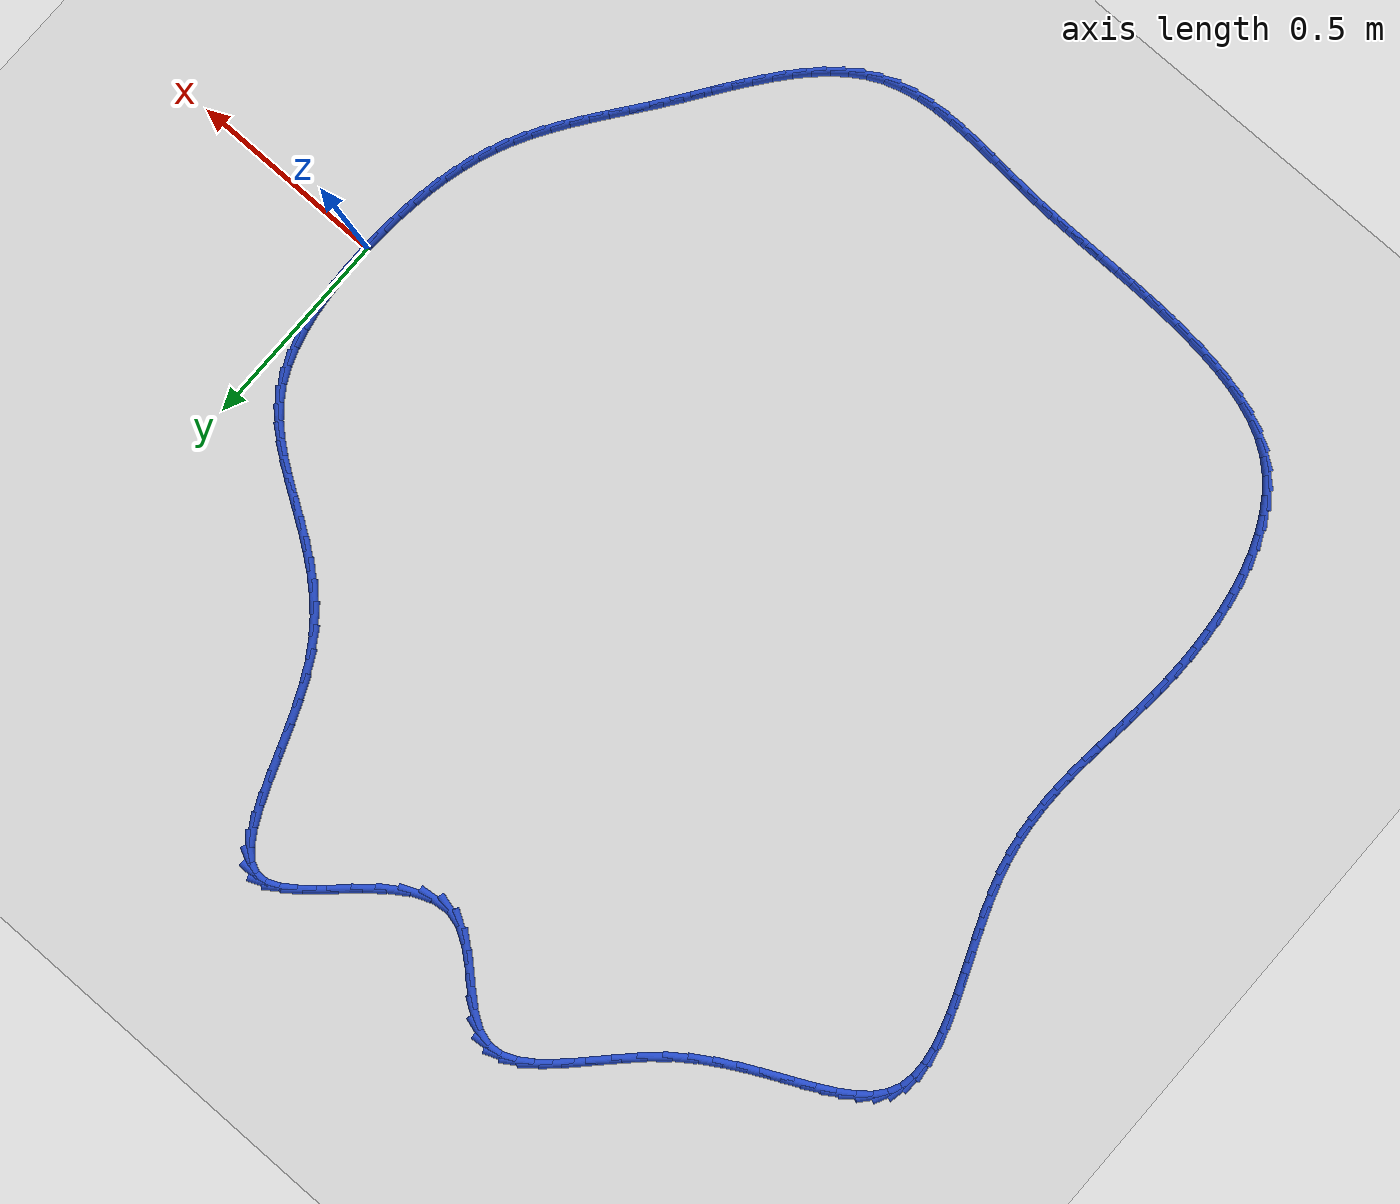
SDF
<sdf version="1.6">
 <world name="default">
  <light name="sun" type="directional">
   <pose>0 0 10 0 -0 0</pose>
   <diffuse>0.8 0.8 0.8 1</diffuse>
   <specular>0.2 0.2 0.2 1</specular>
   <attenuation>
    <range>1000</range>
    <constant>0.9</constant>
    <linear>0.01</linear>
    <quadratic>0.001</quadratic>
   </attenuation>
   <direction>-0.5 0.1 -0.9</direction>
  </light>
  <model name="ground_plane">
   <static>1</static>
   <link name="link">
    <collision name="collision">
     <geometry><plane><normal>0 0 1</normal><size>100 100</size></plane></geometry>
     <surface><friction><ode><mu>100</mu><mu2>50</mu2></ode></friction></surface>
    </collision>
    <visual name="visual">
     <cast_shadows>0</cast_shadows>
     <geometry><plane><normal>0 0 1</normal><size>100 100</size></plane></geometry>
     <material>
      <script><uri>file://media/materials/scripts/gazebo.material</uri><name>Gazebo/WhiteGlow</name></script>
     </material>
    </visual>
   </link>
  </model>
  <gravity>0 0 -9.8</gravity>
  <magnetic_field>6e-06 2.3e-05 -4.2e-05</magnetic_field>
  <atmosphere type="adiabatic"/>
  <physics name="default_physics" default="0" type="ode">
   <max_step_size>0.001</max_step_size>
   <real_time_factor>1</real_time_factor>
   <real_time_update_rate>1000</real_time_update_rate>
  </physics>
  <scene><ambient>0.4 0.4 0.4 1</ambient><background>0.7 0.7 0.7 1</background><shadows>1</shadows></scene>
  <spherical_coordinates>
   <surface_model>EARTH_WGS84</surface_model>
   <latitude_deg>0</latitude_deg>
   <longitude_deg>0</longitude_deg>
   <elevation>0</elevation>
   <heading_deg>0</heading_deg>
  </spherical_coordinates>
  <model name="line">
   <link name="link_0">
    <pose>-6.245004513516506e-17 -5.551115123125783e-17 0.01 0 1.57 1.5629346635734251</pose>
    <collision name="collision">
     <geometry><cylinder><radius>0.01</radius><length>0.08</length></cylinder></geometry>
    </collision>
    <visual name="visual">
     <material>
      <script><name>Gazebo/Blue</name><uri>file://media/materials/scripts/gazebo.material</uri></script>
     </material>
     <geometry><cylinder><radius>0.01</radius><length>0.08</length></cylinder></geometry>
    </visual>
   </link>
   <link name="link_1">
    <pose>0.0003856215391408612 0.0490498745243092 0.01 0 1.57 -1.5426126082793463</pose>
    <collision name="collision">
     <geometry><cylinder><radius>0.01</radius><length>0.08</length></cylinder></geometry>
    </collision>
    <visual name="visual">
     <material>
      <script><name>Gazebo/Blue</name><uri>file://media/materials/scripts/gazebo.material</uri></script>
     </material>
     <geometry><cylinder><radius>0.01</radius><length>0.08</length></cylinder></geometry>
    </visual>
   </link>
   <link name="link_2">
    <pose>-0.0010001237713182748 0.09820514766329383 0.01 0 1.57 -1.4991520352543266</pose>
    <collision name="collision">
     <geometry><cylinder><radius>0.01</radius><length>0.08</length></cylinder></geometry>
    </collision>
    <visual name="visual">
     <material>
      <script><name>Gazebo/Blue</name><uri>file://media/materials/scripts/gazebo.material</uri></script>
     </material>
     <geometry><cylinder><radius>0.01</radius><length>0.08</length></cylinder></geometry>
    </visual>
   </link>
   <link name="link_3">
    <pose>-0.004497198541120264 0.14693323559097243 0.01 0 1.57 -1.4469087028775565</pose>
    <collision name="collision">
     <geometry><cylinder><radius>0.01</radius><length>0.08</length></cylinder></geometry>
    </collision>
    <visual name="visual">
     <material>
      <script><name>Gazebo/Blue</name><uri>file://media/materials/scripts/gazebo.material</uri></script>
     </material>
     <geometry><cylinder><radius>0.01</radius><length>0.08</length></cylinder></geometry>
    </visual>
   </link>
   <link name="link_4">
    <pose>-0.010445565380007899 0.19470155448136353 0.01 0 1.57 -1.3841360880103428</pose>
    <collision name="collision">
     <geometry><cylinder><radius>0.01</radius><length>0.08</length></cylinder></geometry>
    </collision>
    <visual name="visual">
     <material>
      <script><name>Gazebo/Blue</name><uri>file://media/materials/scripts/gazebo.material</uri></script>
     </material>
     <geometry><cylinder><radius>0.01</radius><length>0.08</length></cylinder></geometry>
    </visual>
   </link>
   <link name="link_5">
    <pose>-0.019185186897723965 0.24097752050848564 0.01 0 1.57 -1.3087057582401656</pose>
    <collision name="collision">
     <geometry><cylinder><radius>0.01</radius><length>0.08</length></cylinder></geometry>
    </collision>
    <visual name="visual">
     <material>
      <script><name>Gazebo/Blue</name><uri>file://media/materials/scripts/gazebo.material</uri></script>
     </material>
     <geometry><cylinder><radius>0.01</radius><length>0.08</length></cylinder></geometry>
    </visual>
   </link>
   <link name="link_6">
    <pose>-0.031056025704011277 0.2852285498463573 0.01 0 1.57 -1.2182019126401031</pose>
    <collision name="collision">
     <geometry><cylinder><radius>0.01</radius><length>0.08</length></cylinder></geometry>
    </collision>
    <visual name="visual">
     <material>
      <script><name>Gazebo/Blue</name><uri>file://media/materials/scripts/gazebo.material</uri></script>
     </material>
     <geometry><cylinder><radius>0.01</radius><length>0.08</length></cylinder></geometry>
    </visual>
   </link>
   <link name="link_7">
    <pose>-0.04639804440861261 0.3269220586689971 0.01 0 1.57 -1.1102317523187308</pose>
    <collision name="collision">
     <geometry><cylinder><radius>0.01</radius><length>0.08</length></cylinder></geometry>
    </collision>
    <visual name="visual">
     <material>
      <script><name>Gazebo/Blue</name><uri>file://media/materials/scripts/gazebo.material</uri></script>
     </material>
     <geometry><cylinder><radius>0.01</radius><length>0.08</length></cylinder></geometry>
    </visual>
   </link>
   <link name="link_8">
    <pose>-0.06555120562127074 0.36552546315042345 0.01 0 1.57 -0.9839544452226139</pose>
    <collision name="collision">
     <geometry><cylinder><radius>0.01</radius><length>0.08</length></cylinder></geometry>
    </collision>
    <visual name="visual">
     <material>
      <script><name>Gazebo/Blue</name><uri>file://media/materials/scripts/gazebo.material</uri></script>
     </material>
     <geometry><cylinder><radius>0.01</radius><length>0.08</length></cylinder></geometry>
    </visual>
   </link>
   <link name="link_9">
    <pose>-0.08883316092001198 0.4005363769206715 0.01 0 1.57 -0.8579236870166685</pose>
    <collision name="collision">
     <geometry><cylinder><radius>0.01</radius><length>0.08</length></cylinder></geometry>
    </collision>
    <visual name="visual">
     <material>
      <script><name>Gazebo/Blue</name><uri>file://media/materials/scripts/gazebo.material</uri></script>
     </material>
     <geometry><cylinder><radius>0.01</radius><length>0.08</length></cylinder></geometry>
    </visual>
   </link>
   <link name="link_10">
    <pose>-0.11610058674189572 0.4320763326073782 0.01 0 1.57 -0.753480139657743</pose>
    <collision name="collision">
     <geometry><cylinder><radius>0.01</radius><length>0.08</length></cylinder></geometry>
    </collision>
    <visual name="visual">
     <material>
      <script><name>Gazebo/Blue</name><uri>file://media/materials/scripts/gazebo.material</uri></script>
     </material>
     <geometry><cylinder><radius>0.01</radius><length>0.08</length></cylinder></geometry>
    </visual>
   </link>
   <link name="link_11">
    <pose>-0.14677643418356442 0.4608538998724555 0.01 0 1.57 -0.673907760602511</pose>
    <collision name="collision">
     <geometry><cylinder><radius>0.01</radius><length>0.08</length></cylinder></geometry>
    </collision>
    <visual name="visual">
     <material>
      <script><name>Gazebo/Blue</name><uri>file://media/materials/scripts/gazebo.material</uri></script>
     </material>
     <geometry><cylinder><radius>0.01</radius><length>0.08</length></cylinder></geometry>
    </visual>
   </link>
   <link name="link_12">
    <pose>-0.1802667996139773 0.48760046085481584 0.01 0 1.57 -0.6191192424963969</pose>
    <collision name="collision">
     <geometry><cylinder><radius>0.01</radius><length>0.08</length></cylinder></geometry>
    </collision>
    <visual name="visual">
     <material>
      <script><name>Gazebo/Blue</name><uri>file://media/materials/scripts/gazebo.material</uri></script>
     </material>
     <geometry><cylinder><radius>0.01</radius><length>0.08</length></cylinder></geometry>
    </visual>
   </link>
   <link name="link_13">
    <pose>-0.21597777940209323 0.5130473976933708 0.01 0 1.57 -0.5877596882000896</pose>
    <collision name="collision">
     <geometry><cylinder><radius>0.01</radius><length>0.08</length></cylinder></geometry>
    </collision>
    <visual name="visual">
     <material>
      <script><name>Gazebo/Blue</name><uri>file://media/materials/scripts/gazebo.material</uri></script>
     </material>
     <geometry><cylinder><radius>0.01</radius><length>0.08</length></cylinder></geometry>
    </visual>
   </link>
   <link name="link_14">
    <pose>-0.25331546991687165 0.5379260925270332 0.01 0 1.57 -0.5782236318461663</pose>
    <collision name="collision">
     <geometry><cylinder><radius>0.01</radius><length>0.08</length></cylinder></geometry>
    </collision>
    <visual name="visual">
     <material>
      <script><name>Gazebo/Blue</name><uri>file://media/materials/scripts/gazebo.material</uri></script>
     </material>
     <geometry><cylinder><radius>0.01</radius><length>0.08</length></cylinder></geometry>
    </visual>
   </link>
   <link name="link_15">
    <pose>-0.2916859675272715 0.5629679274947147 0.01 0 1.57 -0.5891331350586869</pose>
    <collision name="collision">
     <geometry><cylinder><radius>0.01</radius><length>0.08</length></cylinder></geometry>
    </collision>
    <visual name="visual">
     <material>
      <script><name>Gazebo/Blue</name><uri>file://media/materials/scripts/gazebo.material</uri></script>
     </material>
     <geometry><cylinder><radius>0.01</radius><length>0.08</length></cylinder></geometry>
    </visual>
   </link>
   <link name="link_16">
    <pose>-0.33049536860225204 0.5889042847353279 0.01 0 1.57 -0.619426323910296</pose>
    <collision name="collision">
     <geometry><cylinder><radius>0.01</radius><length>0.08</length></cylinder></geometry>
    </collision>
    <visual name="visual">
     <material>
      <script><name>Gazebo/Blue</name><uri>file://media/materials/scripts/gazebo.material</uri></script>
     </material>
     <geometry><cylinder><radius>0.01</radius><length>0.08</length></cylinder></geometry>
    </visual>
   </link>
   <link name="link_17">
    <pose>-0.36914976951077255 0.6164665463877846 0.01 0 1.57 -0.6681944307848896</pose>
    <collision name="collision">
     <geometry><cylinder><radius>0.01</radius><length>0.08</length></cylinder></geometry>
    </collision>
    <visual name="visual">
     <material>
      <script><name>Gazebo/Blue</name><uri>file://media/materials/scripts/gazebo.material</uri></script>
     </material>
     <geometry><cylinder><radius>0.01</radius><length>0.08</length></cylinder></geometry>
    </visual>
   </link>
   <link name="link_18">
    <pose>-0.4070552666217917 0.6463860945909969 0.01 0 1.57 -0.7343511809806393</pose>
    <collision name="collision">
     <geometry><cylinder><radius>0.01</radius><length>0.08</length></cylinder></geometry>
    </collision>
    <visual name="visual">
     <material>
      <script><name>Gazebo/Blue</name><uri>file://media/materials/scripts/gazebo.material</uri></script>
     </material>
     <geometry><cylinder><radius>0.01</radius><length>0.08</length></cylinder></geometry>
    </visual>
   </link>
   <link name="link_19">
    <pose>-0.4436179563042692 0.6793943114838776 0.01 0 1.57 -0.8162093784990165</pose>
    <collision name="collision">
     <geometry><cylinder><radius>0.01</radius><length>0.08</length></cylinder></geometry>
    </collision>
    <visual name="visual">
     <material>
      <script><name>Gazebo/Blue</name><uri>file://media/materials/scripts/gazebo.material</uri></script>
     </material>
     <geometry><cylinder><radius>0.01</radius><length>0.08</length></cylinder></geometry>
    </visual>
   </link>
   <link name="link_20">
    <pose>-0.4782439349271637 0.7162225792053383 0.01 0 1.57 -0.9110923795794491</pose>
    <collision name="collision">
     <geometry><cylinder><radius>0.01</radius><length>0.08</length></cylinder></geometry>
    </collision>
    <visual name="visual">
     <material>
      <script><name>Gazebo/Blue</name><uri>file://media/materials/scripts/gazebo.material</uri></script>
     </material>
     <geometry><cylinder><radius>0.01</radius><length>0.08</length></cylinder></geometry>
    </visual>
   </link>
   <link name="link_21">
    <pose>-0.5103392988594349 0.7576022798942916 0.01 0 1.57 -1.0139870729164804</pose>
    <collision name="collision">
     <geometry><cylinder><radius>0.01</radius><length>0.08</length></cylinder></geometry>
    </collision>
    <visual name="visual">
     <material>
      <script><name>Gazebo/Blue</name><uri>file://media/materials/scripts/gazebo.material</uri></script>
     </material>
     <geometry><cylinder><radius>0.01</radius><length>0.08</length></cylinder></geometry>
    </visual>
   </link>
   <link name="link_22">
    <pose>-0.539343731567225 0.8041947375228021 0.01 0 1.57 -1.1013001537380398</pose>
    <collision name="collision">
     <geometry><cylinder><radius>0.01</radius><length>0.08</length></cylinder></geometry>
    </collision>
    <visual name="visual">
     <material>
      <script><name>Gazebo/Blue</name><uri>file://media/materials/scripts/gazebo.material</uri></script>
     </material>
     <geometry><cylinder><radius>0.01</radius><length>0.08</length></cylinder></geometry>
    </visual>
   </link>
   <link name="link_23">
    <pose>-0.5653114168546742 0.8553795110157212 0.01 0 1.57 -1.1602114194753708</pose>
    <collision name="collision">
     <geometry><cylinder><radius>0.01</radius><length>0.08</length></cylinder></geometry>
    </collision>
    <visual name="visual">
     <material>
      <script><name>Gazebo/Blue</name><uri>file://media/materials/scripts/gazebo.material</uri></script>
     </material>
     <geometry><cylinder><radius>0.01</radius><length>0.08</length></cylinder></geometry>
    </visual>
   </link>
   <link name="link_24">
    <pose>-0.5888342883350056 0.9094144855301137 0.01 0 1.57 -1.195839198289286</pose>
    <collision name="collision">
     <geometry><cylinder><radius>0.01</radius><length>0.08</length></cylinder></geometry>
    </collision>
    <visual name="visual">
     <material>
      <script><name>Gazebo/Blue</name><uri>file://media/materials/scripts/gazebo.material</uri></script>
     </material>
     <geometry><cylinder><radius>0.01</radius><length>0.08</length></cylinder></geometry>
    </visual>
   </link>
   <link name="link_25">
    <pose>-0.6105224309104185 0.9645196850758107 0.01 0 1.57 -1.2109751312229877</pose>
    <collision name="collision">
     <geometry><cylinder><radius>0.01</radius><length>0.08</length></cylinder></geometry>
    </collision>
    <visual name="visual">
     <material>
      <script><name>Gazebo/Blue</name><uri>file://media/materials/scripts/gazebo.material</uri></script>
     </material>
     <geometry><cylinder><radius>0.01</radius><length>0.08</length></cylinder></geometry>
    </visual>
   </link>
   <link name="link_26">
    <pose>-0.6309859294831125 1.0189151336626436 0.01 0 1.57 -1.2055506020407951</pose>
    <collision name="collision">
     <geometry><cylinder><radius>0.01</radius><length>0.08</length></cylinder></geometry>
    </collision>
    <visual name="visual">
     <material>
      <script><name>Gazebo/Blue</name><uri>file://media/materials/scripts/gazebo.material</uri></script>
     </material>
     <geometry><cylinder><radius>0.01</radius><length>0.08</length></cylinder></geometry>
    </visual>
   </link>
   <link name="link_27">
    <pose>-0.6508348689552872 1.0708208553004435 0.01 0 1.57 -1.176074536887426</pose>
    <collision name="collision">
     <geometry><cylinder><radius>0.01</radius><length>0.08</length></cylinder></geometry>
    </collision>
    <visual name="visual">
     <material>
      <script><name>Gazebo/Blue</name><uri>file://media/materials/scripts/gazebo.material</uri></script>
     </material>
     <geometry><cylinder><radius>0.01</radius><length>0.08</length></cylinder></geometry>
    </visual>
   </link>
   <link name="link_28">
    <pose>-0.6706793342291418 1.1184568739990417 0.01 0 1.57 -1.1137706009961483</pose>
    <collision name="collision">
     <geometry><cylinder><radius>0.01</radius><length>0.08</length></cylinder></geometry>
    </collision>
    <visual name="visual">
     <material>
      <script><name>Gazebo/Blue</name><uri>file://media/materials/scripts/gazebo.material</uri></script>
     </material>
     <geometry><cylinder><radius>0.01</radius><length>0.08</length></cylinder></geometry>
    </visual>
   </link>
   <link name="link_29">
    <pose>-0.6911294102068758 1.1600432137682695 0.01 0 1.57 -1.0001918787041724</pose>
    <collision name="collision">
     <geometry><cylinder><radius>0.01</radius><length>0.08</length></cylinder></geometry>
    </collision>
    <visual name="visual">
     <material>
      <script><name>Gazebo/Blue</name><uri>file://media/materials/scripts/gazebo.material</uri></script>
     </material>
     <geometry><cylinder><radius>0.01</radius><length>0.08</length></cylinder></geometry>
    </visual>
   </link>
   <link name="link_30">
    <pose>-0.7127951817906886 1.193799898617958 0.01 0 1.57 -0.7991571823419268</pose>
    <collision name="collision">
     <geometry><cylinder><radius>0.01</radius><length>0.08</length></cylinder></geometry>
    </collision>
    <visual name="visual">
     <material>
      <script><name>Gazebo/Blue</name><uri>file://media/materials/scripts/gazebo.material</uri></script>
     </material>
     <geometry><cylinder><radius>0.01</radius><length>0.08</length></cylinder></geometry>
    </visual>
   </link>
   <link name="link_31">
    <pose>-0.7362867338827799 1.2179469525579385 0.01 0 1.57 -0.45726309812766225</pose>
    <collision name="collision">
     <geometry><cylinder><radius>0.01</radius><length>0.08</length></cylinder></geometry>
    </collision>
    <visual name="visual">
     <material>
      <script><name>Gazebo/Blue</name><uri>file://media/materials/scripts/gazebo.material</uri></script>
     </material>
     <geometry><cylinder><radius>0.01</radius><length>0.08</length></cylinder></geometry>
    </visual>
   </link>
   <link name="link_32">
    <pose>-0.762214151385349 1.230704399598042 0.01 0 1.57 0.014078933994974795</pose>
    <collision name="collision">
     <geometry><cylinder><radius>0.01</radius><length>0.08</length></cylinder></geometry>
    </collision>
    <visual name="visual">
     <material>
      <script><name>Gazebo/Blue</name><uri>file://media/materials/scripts/gazebo.material</uri></script>
     </material>
     <geometry><cylinder><radius>0.01</radius><length>0.08</length></cylinder></geometry>
    </visual>
   </link>
   <link name="link_33">
    <pose>-0.7911866044481 1.2302964713906583 0.01 0 1.57 0.4083285465042687</pose>
    <collision name="collision">
     <geometry><cylinder><radius>0.01</radius><length>0.08</length></cylinder></geometry>
    </collision>
    <visual name="visual">
     <material>
      <script><name>Gazebo/Blue</name><uri>file://media/materials/scripts/gazebo.material</uri></script>
     </material>
     <geometry><cylinder><radius>0.01</radius><length>0.08</length></cylinder></geometry>
    </visual>
   </link>
   <link name="link_34">
    <pose>-0.8235173039392557 1.2163087414537976 0.01 0 1.57 0.6102575339565286</pose>
    <collision name="collision">
     <geometry><cylinder><radius>0.01</radius><length>0.08</length></cylinder></geometry>
    </collision>
    <visual name="visual">
     <material>
      <script><name>Gazebo/Blue</name><uri>file://media/materials/scripts/gazebo.material</uri></script>
     </material>
     <geometry><cylinder><radius>0.01</radius><length>0.08</length></cylinder></geometry>
    </visual>
   </link>
   <link name="link_35">
    <pose>-0.8588001687927599 1.191635354061667 0.01 0 1.57 0.7030829358890883</pose>
    <collision name="collision">
     <geometry><cylinder><radius>0.01</radius><length>0.08</length></cylinder></geometry>
    </collision>
    <visual name="visual">
     <material>
      <script><name>Gazebo/Blue</name><uri>file://media/materials/scripts/gazebo.material</uri></script>
     </material>
     <geometry><cylinder><radius>0.01</radius><length>0.08</length></cylinder></geometry>
    </visual>
   </link>
   <link name="link_36">
    <pose>-0.8965219449302791 1.159663423696227 0.01 0 1.57 0.7356043911405161</pose>
    <collision name="collision">
     <geometry><cylinder><radius>0.01</radius><length>0.08</length></cylinder></geometry>
    </collision>
    <visual name="visual">
     <material>
      <script><name>Gazebo/Blue</name><uri>file://media/materials/scripts/gazebo.material</uri></script>
     </material>
     <geometry><cylinder><radius>0.01</radius><length>0.08</length></cylinder></geometry>
    </visual>
   </link>
   <link name="link_37">
    <pose>-0.9361693782734793 1.1237800648394376 0.01 0 1.57 0.7254171050998904</pose>
    <collision name="collision">
     <geometry><cylinder><radius>0.01</radius><length>0.08</length></cylinder></geometry>
    </collision>
    <visual name="visual">
     <material>
      <script><name>Gazebo/Blue</name><uri>file://media/materials/scripts/gazebo.material</uri></script>
     </material>
     <geometry><cylinder><radius>0.01</radius><length>0.08</length></cylinder></geometry>
    </visual>
   </link>
   <link name="link_38">
    <pose>-0.9772292147440271 1.087372391973259 0.01 0 1.57 0.674416557325362</pose>
    <collision name="collision">
     <geometry><cylinder><radius>0.01</radius><length>0.08</length></cylinder></geometry>
    </collision>
    <visual name="visual">
     <material>
      <script><name>Gazebo/Blue</name><uri>file://media/materials/scripts/gazebo.material</uri></script>
     </material>
     <geometry><cylinder><radius>0.01</radius><length>0.08</length></cylinder></geometry>
    </visual>
   </link>
   <link name="link_39">
    <pose>-1.0191882002635881 1.0538275195796518 0.01 0 1.57 0.5725604972261261</pose>
    <collision name="collision">
     <geometry><cylinder><radius>0.01</radius><length>0.08</length></cylinder></geometry>
    </collision>
    <visual name="visual">
     <material>
      <script><name>Gazebo/Blue</name><uri>file://media/materials/scripts/gazebo.material</uri></script>
     </material>
     <geometry><cylinder><radius>0.01</radius><length>0.08</length></cylinder></geometry>
    </visual>
   </link>
   <link name="link_40">
    <pose>-1.0615330807538288 1.026532562140576 0.01 0 1.57 0.3961485390348455</pose>
    <collision name="collision">
     <geometry><cylinder><radius>0.01</radius><length>0.08</length></cylinder></geometry>
    </collision>
    <visual name="visual">
     <material>
      <script><name>Gazebo/Blue</name><uri>file://media/materials/scripts/gazebo.material</uri></script>
     </material>
     <geometry><cylinder><radius>0.01</radius><length>0.08</length></cylinder></geometry>
    </visual>
   </link>
   <link name="link_41">
    <pose>-1.103750602136416 1.0088746341379922 0.01 0 1.57 0.11099285961993188</pose>
    <collision name="collision">
     <geometry><cylinder><radius>0.01</radius><length>0.08</length></cylinder></geometry>
    </collision>
    <visual name="visual">
     <material>
      <script><name>Gazebo/Blue</name><uri>file://media/materials/scripts/gazebo.material</uri></script>
     </material>
     <geometry><cylinder><radius>0.01</radius><length>0.08</length></cylinder></geometry>
    </visual>
   </link>
   <link name="link_42">
    <pose>-1.145327510333015 1.0042408500538604 0.01 0 1.57 -0.2673106754995282</pose>
    <collision name="collision">
     <geometry><cylinder><radius>0.01</radius><length>0.08</length></cylinder></geometry>
    </collision>
    <visual name="visual">
     <material>
      <script><name>Gazebo/Blue</name><uri>file://media/materials/scripts/gazebo.material</uri></script>
     </material>
     <geometry><cylinder><radius>0.01</radius><length>0.08</length></cylinder></geometry>
    </visual>
   </link>
   <link name="link_43">
    <pose>-1.185801704541654 1.015325313987004 0.01 0 1.57 -0.5500484894430149</pose>
    <collision name="collision">
     <geometry><cylinder><radius>0.01</radius><length>0.08</length></cylinder></geometry>
    </collision>
    <visual name="visual">
     <material>
      <script><name>Gazebo/Blue</name><uri>file://media/materials/scripts/gazebo.material</uri></script>
     </material>
     <geometry><cylinder><radius>0.01</radius><length>0.08</length></cylinder></geometry>
    </visual>
   </link>
   <link name="link_44">
    <pose>-1.2251092704457418 1.0394276101067481 0.01 0 1.57 -0.6948070857699192</pose>
    <collision name="collision">
     <geometry><cylinder><radius>0.01</radius><length>0.08</length></cylinder></geometry>
    </collision>
    <visual name="visual">
     <material>
      <script><name>Gazebo/Blue</name><uri>file://media/materials/scripts/gazebo.material</uri></script>
     </material>
     <geometry><cylinder><radius>0.01</radius><length>0.08</length></cylinder></geometry>
    </visual>
   </link>
   <link name="link_45">
    <pose>-1.2633729558371893 1.071318476171559 0.01 0 1.57 -0.7449077804855623</pose>
    <collision name="collision">
     <geometry><cylinder><radius>0.01</radius><length>0.08</length></cylinder></geometry>
    </collision>
    <visual name="visual">
     <material>
      <script><name>Gazebo/Blue</name><uri>file://media/materials/scripts/gazebo.material</uri></script>
     </material>
     <geometry><cylinder><radius>0.01</radius><length>0.08</length></cylinder></geometry>
    </visual>
   </link>
   <link name="link_46">
    <pose>-1.3007165795532272 1.1057541397153545 0.01 0 1.57 -0.7150632096865299</pose>
    <collision name="collision">
     <geometry><cylinder><radius>0.01</radius><length>0.08</length></cylinder></geometry>
    </collision>
    <visual name="visual">
     <material>
      <script><name>Gazebo/Blue</name><uri>file://media/materials/scripts/gazebo.material</uri></script>
     </material>
     <geometry><cylinder><radius>0.01</radius><length>0.08</length></cylinder></geometry>
    </visual>
   </link>
   <link name="link_47">
    <pose>-1.337263960431084 1.1374908282720522 0.01 0 1.57 -0.5856310860886405</pose>
    <collision name="collision">
     <geometry><cylinder><radius>0.01</radius><length>0.08</length></cylinder></geometry>
    </collision>
    <visual name="visual">
     <material>
      <script><name>Gazebo/Blue</name><uri>file://media/materials/scripts/gazebo.material</uri></script>
     </material>
     <geometry><cylinder><radius>0.01</radius><length>0.08</length></cylinder></geometry>
    </visual>
   </link>
   <link name="link_48">
    <pose>-1.3731389173079915 1.16128476937557 0.01 0 1.57 -0.30109135553639543</pose>
    <collision name="collision">
     <geometry><cylinder><radius>0.01</radius><length>0.08</length></cylinder></geometry>
    </collision>
    <visual name="visual">
     <material>
      <script><name>Gazebo/Blue</name><uri>file://media/materials/scripts/gazebo.material</uri></script>
     </material>
     <geometry><cylinder><radius>0.01</radius><length>0.08</length></cylinder></geometry>
    </visual>
   </link>
   <link name="link_49">
    <pose>-1.4084746636536947 1.1722576649102554 0.01 0 1.57 0.07181933834771394</pose>
    <collision name="collision">
     <geometry><cylinder><radius>0.01</radius><length>0.08</length></cylinder></geometry>
    </collision>
    <visual name="visual">
     <material>
      <script><name>Gazebo/Blue</name><uri>file://media/materials/scripts/gazebo.material</uri></script>
     </material>
     <geometry><cylinder><radius>0.01</radius><length>0.08</length></cylinder></geometry>
    </visual>
   </link>
   <link name="link_50">
    <pose>-1.4435125222052843 1.1697369336089687 0.01 0 1.57 0.3798571072307815</pose>
    <collision name="collision">
     <geometry><cylinder><radius>0.01</radius><length>0.08</length></cylinder></geometry>
    </collision>
    <visual name="visual">
     <material>
      <script><name>Gazebo/Blue</name><uri>file://media/materials/scripts/gazebo.material</uri></script>
     </material>
     <geometry><cylinder><radius>0.01</radius><length>0.08</length></cylinder></geometry>
    </visual>
   </link>
   <link name="link_51">
    <pose>-1.478563043257293 1.1557431167450538 0.01 0 1.57 0.5844545792556328</pose>
    <collision name="collision">
     <geometry><cylinder><radius>0.01</radius><length>0.08</length></cylinder></geometry>
    </collision>
    <visual name="visual">
     <material>
      <script><name>Gazebo/Blue</name><uri>file://media/materials/scripts/gazebo.material</uri></script>
     </material>
     <geometry><cylinder><radius>0.01</radius><length>0.08</length></cylinder></geometry>
    </visual>
   </link>
   <link name="link_52">
    <pose>-1.5139379077421848 1.1323407401929177 0.01 0 1.57 0.706701061994898</pose>
    <collision name="collision">
     <geometry><cylinder><radius>0.01</radius><length>0.08</length></cylinder></geometry>
    </collision>
    <visual name="visual">
     <material>
      <script><name>Gazebo/Blue</name><uri>file://media/materials/scripts/gazebo.material</uri></script>
     </material>
     <geometry><cylinder><radius>0.01</radius><length>0.08</length></cylinder></geometry>
    </visual>
   </link>
   <link name="link_53">
    <pose>-1.5499487965924246 1.1015943298269695 0.01 0 1.57 0.7726197663643234</pose>
    <collision name="collision">
     <geometry><cylinder><radius>0.01</radius><length>0.08</length></cylinder></geometry>
    </collision>
    <visual name="visual">
     <material>
      <script><name>Gazebo/Blue</name><uri>file://media/materials/scripts/gazebo.material</uri></script>
     </material>
     <geometry><cylinder><radius>0.01</radius><length>0.08</length></cylinder></geometry>
    </visual>
   </link>
   <link name="link_54">
    <pose>-1.586907390740476 1.0655684115216166 0.01 0 1.57 0.798603370126141</pose>
    <collision name="collision">
     <geometry><cylinder><radius>0.01</radius><length>0.08</length></cylinder></geometry>
    </collision>
    <visual name="visual">
     <material>
      <script><name>Gazebo/Blue</name><uri>file://media/materials/scripts/gazebo.material</uri></script>
     </material>
     <geometry><cylinder><radius>0.01</radius><length>0.08</length></cylinder></geometry>
    </visual>
   </link>
   <link name="link_55">
    <pose>-1.625125371118803 1.0263275111512673 0.01 0 1.57 0.7929099450823983</pose>
    <collision name="collision">
     <geometry><cylinder><radius>0.01</radius><length>0.08</length></cylinder></geometry>
    </collision>
    <visual name="visual">
     <material>
      <script><name>Gazebo/Blue</name><uri>file://media/materials/scripts/gazebo.material</uri></script>
     </material>
     <geometry><cylinder><radius>0.01</radius><length>0.08</length></cylinder></geometry>
    </visual>
   </link>
   <link name="link_56">
    <pose>-1.6649144186598703 0.9859361545903289 0.01 0 1.57 0.7583618253003256</pose>
    <collision name="collision">
     <geometry><cylinder><radius>0.01</radius><length>0.08</length></cylinder></geometry>
    </collision>
    <visual name="visual">
     <material>
      <script><name>Gazebo/Blue</name><uri>file://media/materials/scripts/gazebo.material</uri></script>
     </material>
     <geometry><cylinder><radius>0.01</radius><length>0.08</length></cylinder></geometry>
    </visual>
   </link>
   <link name="link_57">
    <pose>-1.7065862142961419 0.9464588677132103 0.01 0 1.57 0.6940042047772175</pose>
    <collision name="collision">
     <geometry><cylinder><radius>0.01</radius><length>0.08</length></cylinder></geometry>
    </collision>
    <visual name="visual">
     <material>
      <script><name>Gazebo/Blue</name><uri>file://media/materials/scripts/gazebo.material</uri></script>
     </material>
     <geometry><cylinder><radius>0.01</radius><length>0.08</length></cylinder></geometry>
    </visual>
   </link>
   <link name="link_58">
    <pose>-1.750451790681399 0.9099587492793393 0.01 0 1.57 0.6097994945973204</pose>
    <collision name="collision">
     <geometry><cylinder><radius>0.01</radius><length>0.08</length></cylinder></geometry>
    </collision>
    <visual name="visual">
     <material>
      <script><name>Gazebo/Blue</name><uri>file://media/materials/scripts/gazebo.material</uri></script>
     </material>
     <geometry><cylinder><radius>0.01</radius><length>0.08</length></cylinder></geometry>
    </visual>
   </link>
   <link name="link_59">
    <pose>-1.79649961226512 0.8777887992454287 0.01 0 1.57 0.539164161176824</pose>
    <collision name="collision">
     <geometry><cylinder><radius>0.01</radius><length>0.08</length></cylinder></geometry>
    </collision>
    <visual name="visual">
     <material>
      <script><name>Gazebo/Blue</name><uri>file://media/materials/scripts/gazebo.material</uri></script>
     </material>
     <geometry><cylinder><radius>0.01</radius><length>0.08</length></cylinder></geometry>
    </visual>
   </link>
   <link name="link_60">
    <pose>-1.8438744495910824 0.8494447172381937 0.01 0 1.57 0.48794612212520955</pose>
    <collision name="collision">
     <geometry><cylinder><radius>0.01</radius><length>0.08</length></cylinder></geometry>
    </collision>
    <visual name="visual">
     <material>
      <script><name>Gazebo/Blue</name><uri>file://media/materials/scripts/gazebo.material</uri></script>
     </material>
     <geometry><cylinder><radius>0.01</radius><length>0.08</length></cylinder></geometry>
    </visual>
   </link>
   <link name="link_61">
    <pose>-1.891584837356002 0.8241222944910426 0.01 0 1.57 0.45644271564045774</pose>
    <collision name="collision">
     <geometry><cylinder><radius>0.01</radius><length>0.08</length></cylinder></geometry>
    </collision>
    <visual name="visual">
     <material>
      <script><name>Gazebo/Blue</name><uri>file://media/materials/scripts/gazebo.material</uri></script>
     </material>
     <geometry><cylinder><radius>0.01</radius><length>0.08</length></cylinder></geometry>
    </visual>
   </link>
   <link name="link_62">
    <pose>-1.9386393102565944 0.8010173222373854 0.01 0 1.57 0.4456626570988399</pose>
    <collision name="collision">
     <geometry><cylinder><radius>0.01</radius><length>0.08</length></cylinder></geometry>
    </collision>
    <visual name="visual">
     <material>
      <script><name>Gazebo/Blue</name><uri>file://media/materials/scripts/gazebo.material</uri></script>
     </material>
     <geometry><cylinder><radius>0.01</radius><length>0.08</length></cylinder></geometry>
    </visual>
   </link>
   <link name="link_63">
    <pose>-1.9840464029895775 0.7793255917106305 0.01 0 1.57 0.45799341398217</pose>
    <collision name="collision">
     <geometry><cylinder><radius>0.01</radius><length>0.08</length></cylinder></geometry>
    </collision>
    <visual name="visual">
     <material>
      <script><name>Gazebo/Blue</name><uri>file://media/materials/scripts/gazebo.material</uri></script>
     </material>
     <geometry><cylinder><radius>0.01</radius><length>0.08</length></cylinder></geometry>
    </visual>
   </link>
   <link name="link_64">
    <pose>-2.0268146502516657 0.7582428941441873 0.01 0 1.57 0.4979654377503438</pose>
    <collision name="collision">
     <geometry><cylinder><radius>0.01</radius><length>0.08</length></cylinder></geometry>
    </collision>
    <visual name="visual">
     <material>
      <script><name>Gazebo/Blue</name><uri>file://media/materials/scripts/gazebo.material</uri></script>
     </material>
     <geometry><cylinder><radius>0.01</radius><length>0.08</length></cylinder></geometry>
    </visual>
   </link>
   <link name="link_65">
    <pose>-2.065952586739577 0.7369650207714649 0.01 0 1.57 0.573145476328834</pose>
    <collision name="collision">
     <geometry><cylinder><radius>0.01</radius><length>0.08</length></cylinder></geometry>
    </collision>
    <visual name="visual">
     <material>
      <script><name>Gazebo/Blue</name><uri>file://media/materials/scripts/gazebo.material</uri></script>
     </material>
     <geometry><cylinder><radius>0.01</radius><length>0.08</length></cylinder></geometry>
    </visual>
   </link>
   <link name="link_66">
    <pose>-2.100468747150028 0.7146877628258718 0.01 0 1.57 0.694637917948779</pose>
    <collision name="collision">
     <geometry><cylinder><radius>0.01</radius><length>0.08</length></cylinder></geometry>
    </collision>
    <visual name="visual">
     <material>
      <script><name>Gazebo/Blue</name><uri>file://media/materials/scripts/gazebo.material</uri></script>
     </material>
     <geometry><cylinder><radius>0.01</radius><length>0.08</length></cylinder></geometry>
    </visual>
   </link>
   <link name="link_67">
    <pose>-2.129371666179733 0.6906069115408172 0.01 0 1.57 0.8747842006141604</pose>
    <collision name="collision">
     <geometry><cylinder><radius>0.01</radius><length>0.08</length></cylinder></geometry>
    </collision>
    <visual name="visual">
     <material>
      <script><name>Gazebo/Blue</name><uri>file://media/materials/scripts/gazebo.material</uri></script>
     </material>
     <geometry><cylinder><radius>0.01</radius><length>0.08</length></cylinder></geometry>
    </visual>
   </link>
   <link name="link_68">
    <pose>-2.151669878525411 0.6639182581497103 0.01 0 1.57 1.1161459454538287</pose>
    <collision name="collision">
     <geometry><cylinder><radius>0.01</radius><length>0.08</length></cylinder></geometry>
    </collision>
    <visual name="visual">
     <material>
      <script><name>Gazebo/Blue</name><uri>file://media/materials/scripts/gazebo.material</uri></script>
     </material>
     <geometry><cylinder><radius>0.01</radius><length>0.08</length></cylinder></geometry>
    </visual>
   </link>
   <link name="link_69">
    <pose>-2.166380612444159 0.6338228661180262 0.01 0 1.57 1.371564963683134</pose>
    <collision name="collision">
     <geometry><cylinder><radius>0.01</radius><length>0.08</length></cylinder></geometry>
    </collision>
    <visual name="visual">
     <material>
      <script><name>Gazebo/Blue</name><uri>file://media/materials/scripts/gazebo.material</uri></script>
     </material>
     <geometry><cylinder><radius>0.01</radius><length>0.08</length></cylinder></geometry>
    </visual>
   </link>
   <link name="link_70">
    <pose>-2.1732206761025865 0.5999460609476662 0.01 0 1.57 -1.567781966604484</pose>
    <collision name="collision">
     <geometry><cylinder><radius>0.01</radius><length>0.08</length></cylinder></geometry>
    </collision>
    <visual name="visual">
     <material>
      <script><name>Gazebo/Blue</name><uri>file://media/materials/scripts/gazebo.material</uri></script>
     </material>
     <geometry><cylinder><radius>0.01</radius><length>0.08</length></cylinder></geometry>
    </visual>
   </link>
   <link name="link_71">
    <pose>-2.1731082270705904 0.562641729577716 0.01 0 1.57 -1.422330211176339</pose>
    <collision name="collision">
     <geometry><cylinder><radius>0.01</radius><length>0.08</length></cylinder></geometry>
    </collision>
    <visual name="visual">
     <material>
      <script><name>Gazebo/Blue</name><uri>file://media/materials/scripts/gazebo.material</uri></script>
     </material>
     <geometry><cylinder><radius>0.01</radius><length>0.08</length></cylinder></geometry>
    </visual>
   </link>
   <link name="link_72">
    <pose>-2.1670797629348977 0.5223355265550066 0.01 0 1.57 -1.321709398650757</pose>
    <collision name="collision">
     <geometry><cylinder><radius>0.01</radius><length>0.08</length></cylinder></geometry>
    </collision>
    <visual name="visual">
     <material>
      <script><name>Gazebo/Blue</name><uri>file://media/materials/scripts/gazebo.material</uri></script>
     </material>
     <geometry><cylinder><radius>0.01</radius><length>0.08</length></cylinder></geometry>
    </visual>
   </link>
   <link name="link_73">
    <pose>-2.156171781282237 0.4794531064263683 0.01 0 1.57 -1.254250785126707</pose>
    <collision name="collision">
     <geometry><cylinder><radius>0.01</radius><length>0.08</length></cylinder></geometry>
    </collision>
    <visual name="visual">
     <material>
      <script><name>Gazebo/Blue</name><uri>file://media/materials/scripts/gazebo.material</uri></script>
     </material>
     <geometry><cylinder><radius>0.01</radius><length>0.08</length></cylinder></geometry>
    </visual>
   </link>
   <link name="link_74">
    <pose>-2.141420779699339 0.43442012373863326 0.01 0 1.57 -1.2115885726325022</pose>
    <collision name="collision">
     <geometry><cylinder><radius>0.01</radius><length>0.08</length></cylinder></geometry>
    </collision>
    <visual name="visual">
     <material>
      <script><name>Gazebo/Blue</name><uri>file://media/materials/scripts/gazebo.material</uri></script>
     </material>
     <geometry><cylinder><radius>0.01</radius><length>0.08</length></cylinder></geometry>
    </visual>
   </link>
   <link name="link_75">
    <pose>-2.12386325577293 0.3876622330386319 0.01 0 1.57 -1.1884133707221465</pose>
    <collision name="collision">
     <geometry><cylinder><radius>0.01</radius><length>0.08</length></cylinder></geometry>
    </collision>
    <visual name="visual">
     <material>
      <script><name>Gazebo/Blue</name><uri>file://media/materials/scripts/gazebo.material</uri></script>
     </material>
     <geometry><cylinder><radius>0.01</radius><length>0.08</length></cylinder></geometry>
    </visual>
   </link>
   <link name="link_76">
    <pose>-2.104535707089741 0.33960508887319507 0.01 0 1.57 -1.1817083478428339</pose>
    <collision name="collision">
     <geometry><cylinder><radius>0.01</radius><length>0.08</length></cylinder></geometry>
    </collision>
    <visual name="visual">
     <material>
      <script><name>Gazebo/Blue</name><uri>file://media/materials/scripts/gazebo.material</uri></script>
     </material>
     <geometry><cylinder><radius>0.01</radius><length>0.08</length></cylinder></geometry>
    </visual>
   </link>
   <link name="link_77">
    <pose>-2.084474631236499 0.2906743457891544 0.01 0 1.57 -1.1901741984455527</pose>
    <collision name="collision">
     <geometry><cylinder><radius>0.01</radius><length>0.08</length></cylinder></geometry>
    </collision>
    <visual name="visual">
     <material>
      <script><name>Gazebo/Blue</name><uri>file://media/materials/scripts/gazebo.material</uri></script>
     </material>
     <geometry><cylinder><radius>0.01</radius><length>0.08</length></cylinder></geometry>
    </visual>
   </link>
   <link name="link_78">
    <pose>-2.0647165257999323 0.24129565833334027 0.01 0 1.57 -1.2139211062499127</pose>
    <collision name="collision">
     <geometry><cylinder><radius>0.01</radius><length>0.08</length></cylinder></geometry>
    </collision>
    <visual name="visual">
     <material>
      <script><name>Gazebo/Blue</name><uri>file://media/materials/scripts/gazebo.material</uri></script>
     </material>
     <geometry><cylinder><radius>0.01</radius><length>0.08</length></cylinder></geometry>
    </visual>
   </link>
   <link name="link_79">
    <pose>-2.0462978883667713 0.1918946810525844 0.01 0 1.57 -1.2543795109562592</pose>
    <collision name="collision">
     <geometry><cylinder><radius>0.01</radius><length>0.08</length></cylinder></geometry>
    </collision>
    <visual name="visual">
     <material>
      <script><name>Gazebo/Blue</name><uri>file://media/materials/scripts/gazebo.material</uri></script>
     </material>
     <geometry><cylinder><radius>0.01</radius><length>0.08</length></cylinder></geometry>
    </visual>
   </link>
   <link name="link_80">
    <pose>-2.030255216523744 0.14289706849371756 0.01 0 1.57 -1.3140357951877089</pose>
    <collision name="collision">
     <geometry><cylinder><radius>0.01</radius><length>0.08</length></cylinder></geometry>
    </collision>
    <visual name="visual">
     <material>
      <script><name>Gazebo/Blue</name><uri>file://media/materials/scripts/gazebo.material</uri></script>
     </material>
     <geometry><cylinder><radius>0.01</radius><length>0.08</length></cylinder></geometry>
    </visual>
   </link>
   <link name="link_81">
    <pose>-2.0176063030357185 0.0947209720609338 0.01 0 1.57 -1.384823080943124</pose>
    <collision name="collision">
     <geometry><cylinder><radius>0.01</radius><length>0.08</length></cylinder></geometry>
    </collision>
    <visual name="visual">
     <material>
      <script><name>Gazebo/Blue</name><uri>file://media/materials/scripts/gazebo.material</uri></script>
     </material>
     <geometry><cylinder><radius>0.01</radius><length>0.08</length></cylinder></geometry>
    </visual>
   </link>
   <link name="link_82">
    <pose>-2.008726880299085 0.04752699082449379 0.01 0 1.57 -1.4522595287237887</pose>
    <collision name="collision">
     <geometry><cylinder><radius>0.01</radius><length>0.08</length></cylinder></geometry>
    </collision>
    <visual name="visual">
     <material>
      <script><name>Gazebo/Blue</name><uri>file://media/materials/scripts/gazebo.material</uri></script>
     </material>
     <geometry><cylinder><radius>0.01</radius><length>0.08</length></cylinder></geometry>
    </visual>
   </link>
   <link name="link_83">
    <pose>-2.0032047574889873 0.0011596609506769394 0.01 0 1.57 -1.5134329677890233</pose>
    <collision name="collision">
     <geometry><cylinder><radius>0.01</radius><length>0.08</length></cylinder></geometry>
    </collision>
    <visual name="visual">
     <material>
      <script><name>Gazebo/Blue</name><uri>file://media/materials/scripts/gazebo.material</uri></script>
     </material>
     <geometry><cylinder><radius>0.01</radius><length>0.08</length></cylinder></geometry>
    </visual>
   </link>
   <link name="link_84">
    <pose>-2.0005794825921495 -0.04455584060456447 0.01 0 1.57 -1.5666211681387152</pose>
    <collision name="collision">
     <geometry><cylinder><radius>0.01</radius><length>0.08</length></cylinder></geometry>
    </collision>
    <visual name="visual">
     <material>
      <script><name>Gazebo/Blue</name><uri>file://media/materials/scripts/gazebo.material</uri></script>
     </material>
     <geometry><cylinder><radius>0.01</radius><length>0.08</length></cylinder></geometry>
    </visual>
   </link>
   <link name="link_85">
    <pose>-2.0003906035952994 -0.08979433688527738 0.01 0 1.57 1.5310484368386441</pose>
    <collision name="collision">
     <geometry><cylinder><radius>0.01</radius><length>0.08</length></cylinder></geometry>
    </collision>
    <visual name="visual">
     <material>
      <script><name>Gazebo/Blue</name><uri>file://media/materials/scripts/gazebo.material</uri></script>
     </material>
     <geometry><cylinder><radius>0.01</radius><length>0.08</length></cylinder></geometry>
    </visual>
   </link>
   <link name="link_86">
    <pose>-2.0021776684851638 -0.13473065093550868 0.01 0 1.57 1.4972262958728033</pose>
    <collision name="collision">
     <geometry><cylinder><radius>0.01</radius><length>0.08</length></cylinder></geometry>
    </collision>
    <visual name="visual">
     <material>
      <script><name>Gazebo/Blue</name><uri>file://media/materials/scripts/gazebo.material</uri></script>
     </material>
     <geometry><cylinder><radius>0.01</radius><length>0.08</length></cylinder></geometry>
    </visual>
   </link>
   <link name="link_87">
    <pose>-2.0054802252484683 -0.179539605799306 0.01 0 1.57 1.473954760836295</pose>
    <collision name="collision">
     <geometry><cylinder><radius>0.01</radius><length>0.08</length></cylinder></geometry>
    </collision>
    <visual name="visual">
     <material>
      <script><name>Gazebo/Blue</name><uri>file://media/materials/scripts/gazebo.material</uri></script>
     </material>
     <geometry><cylinder><radius>0.01</radius><length>0.08</length></cylinder></geometry>
    </visual>
   </link>
   <link name="link_88">
    <pose>-2.0098378218719395 -0.2243960245207146 0.01 0 1.57 1.4613786820729946</pose>
    <collision name="collision">
     <geometry><cylinder><radius>0.01</radius><length>0.08</length></cylinder></geometry>
    </collision>
    <visual name="visual">
     <material>
      <script><name>Gazebo/Blue</name><uri>file://media/materials/scripts/gazebo.material</uri></script>
     </material>
     <geometry><cylinder><radius>0.01</radius><length>0.08</length></cylinder></geometry>
    </visual>
   </link>
   <link name="link_89">
    <pose>-2.014790006342306 -0.26947473014378237 0.01 0 1.57 1.4594125373669866</pose>
    <collision name="collision">
     <geometry><cylinder><radius>0.01</radius><length>0.08</length></cylinder></geometry>
    </collision>
    <visual name="visual">
     <material>
      <script><name>Gazebo/Blue</name><uri>file://media/materials/scripts/gazebo.material</uri></script>
     </material>
     <geometry><cylinder><radius>0.01</radius><length>0.08</length></cylinder></geometry>
    </visual>
   </link>
   <link name="link_90">
    <pose>-2.019876326646292 -0.314950545712556 0.01 0 1.57 1.467791126929945</pose>
    <collision name="collision">
     <geometry><cylinder><radius>0.01</radius><length>0.08</length></cylinder></geometry>
    </collision>
    <visual name="visual">
     <material>
      <script><name>Gazebo/Blue</name><uri>file://media/materials/scripts/gazebo.material</uri></script>
     </material>
     <geometry><cylinder><radius>0.01</radius><length>0.08</length></cylinder></geometry>
    </visual>
   </link>
   <link name="link_91">
    <pose>-2.024636330770625 -0.36099829427108243 0.01 0 1.57 1.486091320437524</pose>
    <collision name="collision">
     <geometry><cylinder><radius>0.01</radius><length>0.08</length></cylinder></geometry>
    </collision>
    <visual name="visual">
     <material>
      <script><name>Gazebo/Blue</name><uri>file://media/materials/scripts/gazebo.material</uri></script>
     </material>
     <geometry><cylinder><radius>0.01</radius><length>0.08</length></cylinder></geometry>
    </visual>
   </link>
   <link name="link_92">
    <pose>-2.0286095667020327 -0.40779279886340947 0.01 0 1.57 1.5137284460687557</pose>
    <collision name="collision">
     <geometry><cylinder><radius>0.01</radius><length>0.08</length></cylinder></geometry>
    </collision>
    <visual name="visual">
     <material>
      <script><name>Gazebo/Blue</name><uri>file://media/materials/scripts/gazebo.material</uri></script>
     </material>
     <geometry><cylinder><radius>0.01</radius><length>0.08</length></cylinder></geometry>
    </visual>
   </link>
   <link name="link_93">
    <pose>-2.031335582427241 -0.4555088825335821 0.01 0 1.57 1.5498265325159046</pose>
    <collision name="collision">
     <geometry><cylinder><radius>0.01</radius><length>0.08</length></cylinder></geometry>
    </collision>
    <visual name="visual">
     <material>
      <script><name>Gazebo/Blue</name><uri>file://media/materials/scripts/gazebo.material</uri></script>
     </material>
     <geometry><cylinder><radius>0.01</radius><length>0.08</length></cylinder></geometry>
    </visual>
   </link>
   <link name="link_94">
    <pose>-2.0323590312181627 -0.5043075859649069 0.01 0 1.57 -1.550459317505168</pose>
    <collision name="collision">
     <geometry><cylinder><radius>0.01</radius><length>0.08</length></cylinder></geometry>
    </collision>
    <visual name="visual">
     <material>
      <script><name>Gazebo/Blue</name><uri>file://media/materials/scripts/gazebo.material</uri></script>
     </material>
     <geometry><cylinder><radius>0.01</radius><length>0.08</length></cylinder></geometry>
    </visual>
   </link>
   <link name="link_95">
    <pose>-2.0313479540760384 -0.55401684911581 0.01 0 1.57 -1.5060086516736975</pose>
    <collision name="collision">
     <geometry><cylinder><radius>0.01</radius><length>0.08</length></cylinder></geometry>
    </collision>
    <visual name="visual">
     <material>
      <script><name>Gazebo/Blue</name><uri>file://media/materials/scripts/gazebo.material</uri></script>
     </material>
     <geometry><cylinder><radius>0.01</radius><length>0.08</length></cylinder></geometry>
    </visual>
   </link>
   <link name="link_96">
    <pose>-2.0280971882047387 -0.6041223096165977 0.01 0 1.57 -1.4574234662155516</pose>
    <collision name="collision">
     <geometry><cylinder><radius>0.01</radius><length>0.08</length></cylinder></geometry>
    </collision>
    <visual name="visual">
     <material>
      <script><name>Gazebo/Blue</name><uri>file://media/materials/scripts/gazebo.material</uri></script>
     </material>
     <geometry><cylinder><radius>0.01</radius><length>0.08</length></cylinder></geometry>
    </visual>
   </link>
   <link name="link_97">
    <pose>-2.022407357946668 -0.6540939819878034 0.01 0 1.57 -1.4034721893111808</pose>
    <collision name="collision">
     <geometry><cylinder><radius>0.01</radius><length>0.08</length></cylinder></geometry>
    </collision>
    <visual name="visual">
     <material>
      <script><name>Gazebo/Blue</name><uri>file://media/materials/scripts/gazebo.material</uri></script>
     </material>
     <geometry><cylinder><radius>0.01</radius><length>0.08</length></cylinder></geometry>
    </visual>
   </link>
   <link name="link_98">
    <pose>-2.01407908764423 -0.7034018807499629 0.01 0 1.57 -1.3427581451526265</pose>
    <collision name="collision">
     <geometry><cylinder><radius>0.01</radius><length>0.08</length></cylinder></geometry>
    </collision>
    <visual name="visual">
     <material>
      <script><name>Gazebo/Blue</name><uri>file://media/materials/scripts/gazebo.material</uri></script>
     </material>
     <geometry><cylinder><radius>0.01</radius><length>0.08</length></cylinder></geometry>
    </visual>
   </link>
   <link name="link_99">
    <pose>-2.0029130016398264 -0.75151602042361 0.01 0 1.57 -1.2736900160090785</pose>
    <collision name="collision">
     <geometry><cylinder><radius>0.01</radius><length>0.08</length></cylinder></geometry>
    </collision>
    <visual name="visual">
     <material>
      <script><name>Gazebo/Blue</name><uri>file://media/materials/scripts/gazebo.material</uri></script>
     </material>
     <geometry><cylinder><radius>0.01</radius><length>0.08</length></cylinder></geometry>
    </visual>
   </link>
   <link name="link_100">
    <pose>-1.9887097242758618 -0.7979064155292802 0.01 0 1.57 -1.1944928344011243</pose>
    <collision name="collision">
     <geometry><cylinder><radius>0.01</radius><length>0.08</length></cylinder></geometry>
    </collision>
    <visual name="visual">
     <material>
      <script><name>Gazebo/Blue</name><uri>file://media/materials/scripts/gazebo.material</uri></script>
     </material>
     <geometry><cylinder><radius>0.01</radius><length>0.08</length></cylinder></geometry>
    </visual>
   </link>
   <link name="link_101">
    <pose>-1.9712698798947392 -0.8420430805875091 0.01 0 1.57 -1.1033003288801815</pose>
    <collision name="collision">
     <geometry><cylinder><radius>0.01</radius><length>0.08</length></cylinder></geometry>
    </collision>
    <visual name="visual">
     <material>
      <script><name>Gazebo/Blue</name><uri>file://media/materials/scripts/gazebo.material</uri></script>
     </material>
     <geometry><cylinder><radius>0.01</radius><length>0.08</length></cylinder></geometry>
    </visual>
   </link>
   <link name="link_102">
    <pose>-1.9503940928388621 -0.8833960301188293 0.01 0 1.57 -0.9983936686877478</pose>
    <collision name="collision">
     <geometry><cylinder><radius>0.01</radius><length>0.08</length></cylinder></geometry>
    </collision>
    <visual name="visual">
     <material>
      <script><name>Gazebo/Blue</name><uri>file://media/materials/scripts/gazebo.material</uri></script>
     </material>
     <geometry><cylinder><radius>0.01</radius><length>0.08</length></cylinder></geometry>
    </visual>
   </link>
   <link name="link_103">
    <pose>-1.9258829874506342 -0.9214352786437768 0.01 0 1.57 -0.8786611227223863</pose>
    <collision name="collision">
     <geometry><cylinder><radius>0.01</radius><length>0.08</length></cylinder></geometry>
    </collision>
    <visual name="visual">
     <material>
      <script><name>Gazebo/Blue</name><uri>file://media/materials/scripts/gazebo.material</uri></script>
     </material>
     <geometry><cylinder><radius>0.01</radius><length>0.08</length></cylinder></geometry>
    </visual>
   </link>
   <link name="link_104">
    <pose>-1.897537188072458 -0.9556308406828864 0.01 0 1.57 -0.7442974219793101</pose>
    <collision name="collision">
     <geometry><cylinder><radius>0.01</radius><length>0.08</length></cylinder></geometry>
    </collision>
    <visual name="visual">
     <material>
      <script><name>Gazebo/Blue</name><uri>file://media/materials/scripts/gazebo.material</uri></script>
     </material>
     <geometry><cylinder><radius>0.01</radius><length>0.08</length></cylinder></geometry>
    </visual>
   </link>
   <link name="link_105">
    <pose>-1.8651573190467372 -0.9854527307566923 0.01 0 1.57 -0.5992207532148043</pose>
    <collision name="collision">
     <geometry><cylinder><radius>0.01</radius><length>0.08</length></cylinder></geometry>
    </collision>
    <visual name="visual">
     <material>
      <script><name>Gazebo/Blue</name><uri>file://media/materials/scripts/gazebo.material</uri></script>
     </material>
     <geometry><cylinder><radius>0.01</radius><length>0.08</length></cylinder></geometry>
    </visual>
   </link>
   <link name="link_106">
    <pose>-1.828594224812803 -1.0104250846201497 0.01 0 1.57 -0.46608468973641887</pose>
    <collision name="collision">
     <geometry><cylinder><radius>0.01</radius><length>0.08</length></cylinder></geometry>
    </collision>
    <visual name="visual">
     <material>
      <script><name>Gazebo/Blue</name><uri>file://media/materials/scripts/gazebo.material</uri></script>
     </material>
     <geometry><cylinder><radius>0.01</radius><length>0.08</length></cylinder></geometry>
    </visual>
   </link>
   <link name="link_107">
    <pose>-1.7882842500460694 -1.0307030203932006 0.01 0 1.57 -0.35736798985334184</pose>
    <collision name="collision">
     <geometry><cylinder><radius>0.01</radius><length>0.08</length></cylinder></geometry>
    </collision>
    <visual name="visual">
     <material>
      <script><name>Gazebo/Blue</name><uri>file://media/materials/scripts/gazebo.material</uri></script>
     </material>
     <geometry><cylinder><radius>0.01</radius><length>0.08</length></cylinder></geometry>
    </visual>
   </link>
   <link name="link_108">
    <pose>-1.7450422863058541 -1.0468496089058736 0.01 0 1.57 -0.2706842790103173</pose>
    <collision name="collision">
     <geometry><cylinder><radius>0.01</radius><length>0.08</length></cylinder></geometry>
    </collision>
    <visual name="visual">
     <material>
      <script><name>Gazebo/Blue</name><uri>file://media/materials/scripts/gazebo.material</uri></script>
     </material>
     <geometry><cylinder><radius>0.01</radius><length>0.08</length></cylinder></geometry>
    </visual>
   </link>
   <link name="link_109">
    <pose>-1.6996895705224537 -1.0594347592726943 0.01 0 1.57 -0.2028561715625097</pose>
    <collision name="collision">
     <geometry><cylinder><radius>0.01</radius><length>0.08</length></cylinder></geometry>
    </collision>
    <visual name="visual">
     <material>
      <script><name>Gazebo/Blue</name><uri>file://media/materials/scripts/gazebo.material</uri></script>
     </material>
     <geometry><cylinder><radius>0.01</radius><length>0.08</length></cylinder></geometry>
    </visual>
   </link>
   <link name="link_110">
    <pose>-1.653047339626166 -1.0690283806081877 0.01 0 1.57 -0.1510778074019528</pose>
    <collision name="collision">
     <geometry><cylinder><radius>0.01</radius><length>0.08</length></cylinder></geometry>
    </collision>
    <visual name="visual">
     <material>
      <script><name>Gazebo/Blue</name><uri>file://media/materials/scripts/gazebo.material</uri></script>
     </material>
     <geometry><cylinder><radius>0.01</radius><length>0.08</length></cylinder></geometry>
    </visual>
   </link>
   <link name="link_111">
    <pose>-1.605936830547287 -1.0762003820268795 0.01 0 1.57 -0.11278991348390137</pose>
    <collision name="collision">
     <geometry><cylinder><radius>0.01</radius><length>0.08</length></cylinder></geometry>
    </collision>
    <visual name="visual">
     <material>
      <script><name>Gazebo/Blue</name><uri>file://media/materials/scripts/gazebo.material</uri></script>
     </material>
     <geometry><cylinder><radius>0.01</radius><length>0.08</length></cylinder></geometry>
    </visual>
   </link>
   <link name="link_112">
    <pose>-1.5591261314909306 -1.0815026602407505 0.01 0 1.57 -0.0818393585840511</pose>
    <collision name="collision">
     <geometry><cylinder><radius>0.01</radius><length>0.08</length></cylinder></geometry>
    </collision>
    <visual name="visual">
     <material>
      <script><name>Gazebo/Blue</name><uri>file://media/materials/scripts/gazebo.material</uri></script>
     </material>
     <geometry><cylinder><radius>0.01</radius><length>0.08</length></cylinder></geometry>
    </visual>
   </link>
   <link name="link_113">
    <pose>-1.5128309560181423 -1.0852999090813884 0.01 0 1.57 -0.05541975274387008</pose>
    <collision name="collision">
     <geometry><cylinder><radius>0.01</radius><length>0.08</length></cylinder></geometry>
    </collision>
    <visual name="visual">
     <material>
      <script><name>Gazebo/Blue</name><uri>file://media/materials/scripts/gazebo.material</uri></script>
     </material>
     <geometry><cylinder><radius>0.01</radius><length>0.08</length></cylinder></geometry>
    </visual>
   </link>
   <link name="link_114">
    <pose>-1.466939460497508 -1.0878458114015428 0.01 0 1.57 -0.03390470617174254</pose>
    <collision name="collision">
     <geometry><cylinder><radius>0.01</radius><length>0.08</length></cylinder></geometry>
    </collision>
    <visual name="visual">
     <material>
      <script><name>Gazebo/Blue</name><uri>file://media/materials/scripts/gazebo.material</uri></script>
     </material>
     <geometry><cylinder><radius>0.01</radius><length>0.08</length></cylinder></geometry>
    </visual>
   </link>
   <link name="link_115">
    <pose>-1.421335501872485 -1.0893925929545543 0.01 0 1.57 -0.017604198902374947</pose>
    <collision name="collision">
     <geometry><cylinder><radius>0.01</radius><length>0.08</length></cylinder></geometry>
    </collision>
    <visual name="visual">
     <material>
      <script><name>Gazebo/Blue</name><uri>file://media/materials/scripts/gazebo.material</uri></script>
     </material>
     <geometry><cylinder><radius>0.01</radius><length>0.08</length></cylinder></geometry>
    </visual>
   </link>
   <link name="link_116">
    <pose>-1.3759029370865306 -1.0901924794937627 0.01 0 1.57 -0.006726107146378662</pose>
    <collision name="collision">
     <geometry><cylinder><radius>0.01</radius><length>0.08</length></cylinder></geometry>
    </collision>
    <visual name="visual">
     <material>
      <script><name>Gazebo/Blue</name><uri>file://media/materials/scripts/gazebo.material</uri></script>
     </material>
     <geometry><cylinder><radius>0.01</radius><length>0.08</length></cylinder></geometry>
    </visual>
   </link>
   <link name="link_117">
    <pose>-1.330525623083104 -1.0904976967725077 0.01 0 1.57 -0.0013815187004142062</pose>
    <collision name="collision">
     <geometry><cylinder><radius>0.01</radius><length>0.08</length></cylinder></geometry>
    </collision>
    <visual name="visual">
     <material>
      <script><name>Gazebo/Blue</name><uri>file://media/materials/scripts/gazebo.material</uri></script>
     </material>
     <geometry><cylinder><radius>0.01</radius><length>0.08</length></cylinder></geometry>
    </visual>
   </link>
   <link name="link_118">
    <pose>-1.285087416805662 -1.0905604705441299 0.01 0 1.57 -0.0015906077462704568</pose>
    <collision name="collision">
     <geometry><cylinder><radius>0.01</radius><length>0.08</length></cylinder></geometry>
    </collision>
    <visual name="visual">
     <material>
      <script><name>Gazebo/Blue</name><uri>file://media/materials/scripts/gazebo.material</uri></script>
     </material>
     <geometry><cylinder><radius>0.01</radius><length>0.08</length></cylinder></geometry>
    </visual>
   </link>
   <link name="link_119">
    <pose>-1.2394721751976634 -1.0906330265619693 0.01 0 1.57 -0.007287510542872682</pose>
    <collision name="collision">
     <geometry><cylinder><radius>0.01</radius><length>0.08</length></cylinder></geometry>
    </collision>
    <visual name="visual">
     <material>
      <script><name>Gazebo/Blue</name><uri>file://media/materials/scripts/gazebo.material</uri></script>
     </material>
     <geometry><cylinder><radius>0.01</radius><length>0.08</length></cylinder></geometry>
    </visual>
   </link>
   <link name="link_120">
    <pose>-1.193563755202565 -1.0909675905793652 0.01 0 1.57 -0.018323492188613184</pose>
    <collision name="collision">
     <geometry><cylinder><radius>0.01</radius><length>0.08</length></cylinder></geometry>
    </collision>
    <visual name="visual">
     <material>
      <script><name>Gazebo/Blue</name><uri>file://media/materials/scripts/gazebo.material</uri></script>
     </material>
     <geometry><cylinder><radius>0.01</radius><length>0.08</length></cylinder></geometry>
    </visual>
   </link>
   <link name="link_121">
    <pose>-1.1472460137638247 -1.0918163883496592 0.01 0 1.57 -0.03446855329202941</pose>
    <collision name="collision">
     <geometry><cylinder><radius>0.01</radius><length>0.08</length></cylinder></geometry>
    </collision>
    <visual name="visual">
     <material>
      <script><name>Gazebo/Blue</name><uri>file://media/materials/scripts/gazebo.material</uri></script>
     </material>
     <geometry><cylinder><radius>0.01</radius><length>0.08</length></cylinder></geometry>
    </visual>
   </link>
   <link name="link_122">
    <pose>-1.100402807824901 -1.0934316456261897 0.01 0 1.57 -0.05523482125030368</pose>
    <collision name="collision">
     <geometry><cylinder><radius>0.01</radius><length>0.08</length></cylinder></geometry>
    </collision>
    <visual name="visual">
     <material>
      <script><name>Gazebo/Blue</name><uri>file://media/materials/scripts/gazebo.material</uri></script>
     </material>
     <geometry><cylinder><radius>0.01</radius><length>0.08</length></cylinder></geometry>
    </visual>
   </link>
   <link name="link_123">
    <pose>-1.0529221714206558 -1.0960569004179075 0.01 0 1.57 -0.07277348778180333</pose>
    <collision name="collision">
     <geometry><cylinder><radius>0.01</radius><length>0.08</length></cylinder></geometry>
    </collision>
    <visual name="visual">
     <material>
      <script><name>Gazebo/Blue</name><uri>file://media/materials/scripts/gazebo.material</uri></script>
     </material>
     <geometry><cylinder><radius>0.01</radius><length>0.08</length></cylinder></geometry>
    </visual>
   </link>
   <link name="link_124">
    <pose>-1.0048728670020302 -1.099559801836212 0.01 0 1.57 -0.07720356190078186</pose>
    <collision name="collision">
     <geometry><cylinder><radius>0.01</radius><length>0.08</length></cylinder></geometry>
    </collision>
    <visual name="visual">
     <material>
      <script><name>Gazebo/Blue</name><uri>file://media/materials/scripts/gazebo.material</uri></script>
     </material>
     <geometry><cylinder><radius>0.01</radius><length>0.08</length></cylinder></geometry>
    </visual>
   </link>
   <link name="link_125">
    <pose>-0.9565696301226694 -1.1032964106080756 0.01 0 1.57 -0.06811118742837162</pose>
    <collision name="collision">
     <geometry><cylinder><radius>0.01</radius><length>0.08</length></cylinder></geometry>
    </collision>
    <visual name="visual">
     <material>
      <script><name>Gazebo/Blue</name><uri>file://media/materials/scripts/gazebo.material</uri></script>
     </material>
     <geometry><cylinder><radius>0.01</radius><length>0.08</length></cylinder></geometry>
    </visual>
   </link>
   <link name="link_126">
    <pose>-0.9083448122224239 -1.106586148971684 0.01 0 1.57 -0.04519211554203356</pose>
    <collision name="collision">
     <geometry><cylinder><radius>0.01</radius><length>0.08</length></cylinder></geometry>
    </collision>
    <visual name="visual">
     <material>
      <script><name>Gazebo/Blue</name><uri>file://media/materials/scripts/gazebo.material</uri></script>
     </material>
     <geometry><cylinder><radius>0.01</radius><length>0.08</length></cylinder></geometry>
    </visual>
   </link>
   <link name="link_127">
    <pose>-0.860530764741148 -1.1087484391652236 0.01 0 1.57 -0.007526037958479634</pose>
    <collision name="collision">
     <geometry><cylinder><radius>0.01</radius><length>0.08</length></cylinder></geometry>
    </collision>
    <visual name="visual">
     <material>
      <script><name>Gazebo/Blue</name><uri>file://media/materials/scripts/gazebo.material</uri></script>
     </material>
     <geometry><cylinder><radius>0.01</radius><length>0.08</length></cylinder></geometry>
    </visual>
   </link>
   <link name="link_128">
    <pose>-0.8134598391186921 -1.1091027034268808 0.01 0 1.57 0.04637000765670856</pose>
    <collision name="collision">
     <geometry><cylinder><radius>0.01</radius><length>0.08</length></cylinder></geometry>
    </collision>
    <visual name="visual">
     <material>
      <script><name>Gazebo/Blue</name><uri>file://media/materials/scripts/gazebo.material</uri></script>
     </material>
     <geometry><cylinder><radius>0.01</radius><length>0.08</length></cylinder></geometry>
    </visual>
   </link>
   <link name="link_129">
    <pose>-0.7674643867949082 -1.1069683639948416 0.01 0 1.57 0.11838977968641326</pose>
    <collision name="collision">
     <geometry><cylinder><radius>0.01</radius><length>0.08</length></cylinder></geometry>
    </collision>
    <visual name="visual">
     <material>
      <script><name>Gazebo/Blue</name><uri>file://media/materials/scripts/gazebo.material</uri></script>
     </material>
     <geometry><cylinder><radius>0.01</radius><length>0.08</length></cylinder></geometry>
    </visual>
   </link>
   <link name="link_130">
    <pose>-0.7228767592096484 -1.1016648431072933 0.01 0 1.57 0.21046139087946278</pose>
    <collision name="collision">
     <geometry><cylinder><radius>0.01</radius><length>0.08</length></cylinder></geometry>
    </collision>
    <visual name="visual">
     <material>
      <script><name>Gazebo/Blue</name><uri>file://media/materials/scripts/gazebo.material</uri></script>
     </material>
     <geometry><cylinder><radius>0.01</radius><length>0.08</length></cylinder></geometry>
    </visual>
   </link>
   <link name="link_131">
    <pose>-0.6800293078027635 -1.0925115630024214 0.01 0 1.57 0.32377930488738954</pose>
    <collision name="collision">
     <geometry><cylinder><radius>0.01</radius><length>0.08</length></cylinder></geometry>
    </collision>
    <visual name="visual">
     <material>
      <script><name>Gazebo/Blue</name><uri>file://media/materials/scripts/gazebo.material</uri></script>
     </material>
     <geometry><cylinder><radius>0.01</radius><length>0.08</length></cylinder></geometry>
    </visual>
   </link>
   <link name="link_132">
    <pose>-0.6392543840141073 -1.0788279459184125 0.01 0 1.57 0.453035742132471</pose>
    <collision name="collision">
     <geometry><cylinder><radius>0.01</radius><length>0.08</length></cylinder></geometry>
    </collision>
    <visual name="visual">
     <material>
      <script><name>Gazebo/Blue</name><uri>file://media/materials/scripts/gazebo.material</uri></script>
     </material>
     <geometry><cylinder><radius>0.01</radius><length>0.08</length></cylinder></geometry>
    </visual>
   </link>
   <link name="link_133">
    <pose>-0.6008020848001012 -1.0601091865289118 0.01 0 1.57 0.5734678319440709</pose>
    <collision name="collision">
     <geometry><cylinder><radius>0.01</radius><length>0.08</length></cylinder></geometry>
    </collision>
    <visual name="visual">
     <material>
      <script><name>Gazebo/Blue</name><uri>file://media/materials/scripts/gazebo.material</uri></script>
     </material>
     <geometry><cylinder><radius>0.01</radius><length>0.08</length></cylinder></geometry>
    </visual>
   </link>
   <link name="link_134">
    <pose>-0.5645325801109076 -1.0366837279419878 0.01 0 1.57 0.676221440087815</pose>
    <collision name="collision">
     <geometry><cylinder><radius>0.01</radius><length>0.08</length></cylinder></geometry>
    </collision>
    <visual name="visual">
     <material>
      <script><name>Gazebo/Blue</name><uri>file://media/materials/scripts/gazebo.material</uri></script>
     </material>
     <geometry><cylinder><radius>0.01</radius><length>0.08</length></cylinder></geometry>
    </visual>
   </link>
   <link name="link_135">
    <pose>-0.530190613176374 -1.0091266725953971 0.01 0 1.57 0.7610048643150867</pose>
    <collision name="collision">
     <geometry><cylinder><radius>0.01</radius><length>0.08</length></cylinder></geometry>
    </collision>
    <visual name="visual">
     <material>
      <script><name>Gazebo/Blue</name><uri>file://media/materials/scripts/gazebo.material</uri></script>
     </material>
     <geometry><cylinder><radius>0.01</radius><length>0.08</length></cylinder></geometry>
    </visual>
   </link>
   <link name="link_136">
    <pose>-0.4975209095513707 -0.9780131606971633 0.01 0 1.57 0.8288630490720164</pose>
    <collision name="collision">
     <geometry><cylinder><radius>0.01</radius><length>0.08</length></cylinder></geometry>
    </collision>
    <visual name="visual">
     <material>
      <script><name>Gazebo/Blue</name><uri>file://media/materials/scripts/gazebo.material</uri></script>
     </material>
     <geometry><cylinder><radius>0.01</radius><length>0.08</length></cylinder></geometry>
    </visual>
   </link>
   <link name="link_137">
    <pose>-0.46626819479076953 -0.9439183324553125 0.01 0 1.57 0.881360372986391</pose>
    <collision name="collision">
     <geometry><cylinder><radius>0.01</radius><length>0.08</length></cylinder></geometry>
    </collision>
    <visual name="visual">
     <material>
      <script><name>Gazebo/Blue</name><uri>file://media/materials/scripts/gazebo.material</uri></script>
     </material>
     <geometry><cylinder><radius>0.01</radius><length>0.08</length></cylinder></geometry>
    </visual>
   </link>
   <link name="link_138">
    <pose>-0.43617719444944075 -0.9074173280778685 0.01 0 1.57 0.9200630822638568</pose>
    <collision name="collision">
     <geometry><cylinder><radius>0.01</radius><length>0.08</length></cylinder></geometry>
    </collision>
    <visual name="visual">
     <material>
      <script><name>Gazebo/Blue</name><uri>file://media/materials/scripts/gazebo.material</uri></script>
     </material>
     <geometry><cylinder><radius>0.01</radius><length>0.08</length></cylinder></geometry>
    </visual>
   </link>
   <link name="link_139">
    <pose>-0.4069926340822549 -0.8690852877728553 0.01 0 1.57 0.946273025899692</pose>
    <collision name="collision">
     <geometry><cylinder><radius>0.01</radius><length>0.08</length></cylinder></geometry>
    </collision>
    <visual name="visual">
     <material>
      <script><name>Gazebo/Blue</name><uri>file://media/materials/scripts/gazebo.material</uri></script>
     </material>
     <geometry><cylinder><radius>0.01</radius><length>0.08</length></cylinder></geometry>
    </visual>
   </link>
   <link name="link_140">
    <pose>-0.3784592392440828 -0.8294973517482975 0.01 0 1.57 0.9609138603806536</pose>
    <collision name="collision">
     <geometry><cylinder><radius>0.01</radius><length>0.08</length></cylinder></geometry>
    </collision>
    <visual name="visual">
     <material>
      <script><name>Gazebo/Blue</name><uri>file://media/materials/scripts/gazebo.material</uri></script>
     </material>
     <geometry><cylinder><radius>0.01</radius><length>0.08</length></cylinder></geometry>
    </visual>
   </link>
   <link name="link_141">
    <pose>-0.3503217354897947 -0.7892286602122186 0.01 0 1.57 0.9644911817865477</pose>
    <collision name="collision">
     <geometry><cylinder><radius>0.01</radius><length>0.08</length></cylinder></geometry>
    </collision>
    <visual name="visual">
     <material>
      <script><name>Gazebo/Blue</name><uri>file://media/materials/scripts/gazebo.material</uri></script>
     </material>
     <geometry><cylinder><radius>0.01</radius><length>0.08</length></cylinder></geometry>
    </visual>
   </link>
   <link name="link_142">
    <pose>-0.3223248483742622 -0.7488543533726447 0.01 0 1.57 0.9570796193301473</pose>
    <collision name="collision">
     <geometry><cylinder><radius>0.01</radius><length>0.08</length></cylinder></geometry>
    </collision>
    <visual name="visual">
     <material>
      <script><name>Gazebo/Blue</name><uri>file://media/materials/scripts/gazebo.material</uri></script>
     </material>
     <geometry><cylinder><radius>0.01</radius><length>0.08</length></cylinder></geometry>
    </visual>
   </link>
   <link name="link_143">
    <pose>-0.29421330345235547 -0.7089495714375991 0.01 0 1.57 0.9413193991657214</pose>
    <collision name="collision">
     <geometry><cylinder><radius>0.01</radius><length>0.08</length></cylinder></geometry>
    </collision>
    <visual name="visual">
     <material>
      <script><name>Gazebo/Blue</name><uri>file://media/materials/scripts/gazebo.material</uri></script>
     </material>
     <geometry><cylinder><radius>0.01</radius><length>0.08</length></cylinder></geometry>
    </visual>
   </link>
   <link name="link_144">
    <pose>-0.2658207336164107 -0.6699655974616125 0.01 0 1.57 0.9307517420017201</pose>
    <collision name="collision">
     <geometry><cylinder><radius>0.01</radius><length>0.08</length></cylinder></geometry>
    </collision>
    <visual name="visual">
     <material>
      <script><name>Gazebo/Blue</name><uri>file://media/materials/scripts/gazebo.material</uri></script>
     </material>
     <geometry><cylinder><radius>0.01</radius><length>0.08</length></cylinder></geometry>
    </visual>
   </link>
   <link name="link_145">
    <pose>-0.23738996558489137 -0.6317836650075063 0.01 0 1.57 0.9296515686998654</pose>
    <collision name="collision">
     <geometry><cylinder><radius>0.01</radius><length>0.08</length></cylinder></geometry>
    </collision>
    <visual name="visual">
     <material>
      <script><name>Gazebo/Blue</name><uri>file://media/materials/scripts/gazebo.material</uri></script>
     </material>
     <geometry><cylinder><radius>0.01</radius><length>0.08</length></cylinder></geometry>
    </visual>
   </link>
   <link name="link_146">
    <pose>-0.20928147315051904 -0.5941211130468343 0.01 0 1.57 0.9383931516124392</pose>
    <collision name="collision">
     <geometry><cylinder><radius>0.01</radius><length>0.08</length></cylinder></geometry>
    </collision>
    <visual name="visual">
     <material>
      <script><name>Gazebo/Blue</name><uri>file://media/materials/scripts/gazebo.material</uri></script>
     </material>
     <geometry><cylinder><radius>0.01</radius><length>0.08</length></cylinder></geometry>
    </visual>
   </link>
   <link name="link_147">
    <pose>-0.18185574056341902 -0.5566952659829052 0.01 0 1.57 0.9573492884447119</pose>
    <collision name="collision">
     <geometry><cylinder><radius>0.01</radius><length>0.08</length></cylinder></geometry>
    </collision>
    <visual name="visual">
     <material>
      <script><name>Gazebo/Blue</name><uri>file://media/materials/scripts/gazebo.material</uri></script>
     </material>
     <geometry><cylinder><radius>0.01</radius><length>0.08</length></cylinder></geometry>
    </visual>
   </link>
   <link name="link_148">
    <pose>-0.15547325207371482 -0.519223448219025 0.01 0 1.57 0.9868623352196985</pose>
    <collision name="collision">
     <geometry><cylinder><radius>0.01</radius><length>0.08</length></cylinder></geometry>
    </collision>
    <visual name="visual">
     <material>
      <script><name>Gazebo/Blue</name><uri>file://media/materials/scripts/gazebo.material</uri></script>
     </material>
     <geometry><cylinder><radius>0.01</radius><length>0.08</length></cylinder></geometry>
    </visual>
   </link>
   <link name="link_149">
    <pose>-0.13049449193153073 -0.4814229841585017 0.01 0 1.57 1.0271770986971842</pose>
    <collision name="collision">
     <geometry><cylinder><radius>0.01</radius><length>0.08</length></cylinder></geometry>
    </collision>
    <visual name="visual">
     <material>
      <script><name>Gazebo/Blue</name><uri>file://media/materials/scripts/gazebo.material</uri></script>
     </material>
     <geometry><cylinder><radius>0.01</radius><length>0.08</length></cylinder></geometry>
    </visual>
   </link>
   <link name="link_150">
    <pose>-0.10727994438699091 -0.44301119820464235 0.01 0 1.57 1.0783314507851085</pose>
    <collision name="collision">
     <geometry><cylinder><radius>0.01</radius><length>0.08</length></cylinder></geometry>
    </collision>
    <visual name="visual">
     <material>
      <script><name>Gazebo/Blue</name><uri>file://media/materials/scripts/gazebo.material</uri></script>
     </material>
     <geometry><cylinder><radius>0.01</radius><length>0.08</length></cylinder></geometry>
    </visual>
   </link>
   <link name="link_151">
    <pose>-0.08619009369021914 -0.4037054147607534 0.01 0 1.57 1.1397613733833982</pose>
    <collision name="collision">
     <geometry><cylinder><radius>0.01</radius><length>0.08</length></cylinder></geometry>
    </collision>
    <visual name="visual">
     <material>
      <script><name>Gazebo/Blue</name><uri>file://media/materials/scripts/gazebo.material</uri></script>
     </material>
     <geometry><cylinder><radius>0.01</radius><length>0.08</length></cylinder></geometry>
    </visual>
   </link>
   <link name="link_152">
    <pose>-0.06757627257473318 -0.36322952201407216 0.01 0 1.57 1.2043940502115094</pose>
    <collision name="collision">
     <geometry><cylinder><radius>0.01</radius><length>0.08</length></cylinder></geometry>
    </collision>
    <visual name="visual">
     <material>
      <script><name>Gazebo/Blue</name><uri>file://media/materials/scripts/gazebo.material</uri></script>
     </material>
     <geometry><cylinder><radius>0.01</radius><length>0.08</length></cylinder></geometry>
    </visual>
   </link>
   <link name="link_153">
    <pose>-0.05155431636760178 -0.3214763150290196 0.01 0 1.57 1.2649428699784944</pose>
    <collision name="collision">
     <geometry><cylinder><radius>0.01</radius><length>0.08</length></cylinder></geometry>
    </collision>
    <visual name="visual">
     <material>
      <script><name>Gazebo/Blue</name><uri>file://media/materials/scripts/gazebo.material</uri></script>
     </material>
     <geometry><cylinder><radius>0.01</radius><length>0.08</length></cylinder></geometry>
    </visual>
   </link>
   <link name="link_154">
    <pose>-0.03798976731864339 -0.2785181077135473 0.01 0 1.57 1.3208457606370694</pose>
    <collision name="collision">
     <geometry><cylinder><radius>0.01</radius><length>0.08</length></cylinder></geometry>
    </collision>
    <visual name="visual">
     <material>
      <script><name>Gazebo/Blue</name><uri>file://media/materials/scripts/gazebo.material</uri></script>
     </material>
     <geometry><cylinder><radius>0.01</radius><length>0.08</length></cylinder></geometry>
    </visual>
   </link>
   <link name="link_155">
    <pose>-0.026736053582384317 -0.23443590262333555 0.01 0 1.57 1.372028676478435</pose>
    <collision name="collision">
     <geometry><cylinder><radius>0.01</radius><length>0.08</length></cylinder></geometry>
    </collision>
    <visual name="visual">
     <material>
      <script><name>Gazebo/Blue</name><uri>file://media/materials/scripts/gazebo.material</uri></script>
     </material>
     <geometry><cylinder><radius>0.01</radius><length>0.08</length></cylinder></geometry>
    </visual>
   </link>
   <link name="link_156">
    <pose>-0.017646603313350738 -0.18931070231406402 0.01 0 1.57 1.4185408228997154</pose>
    <collision name="collision">
     <geometry><cylinder><radius>0.01</radius><length>0.08</length></cylinder></geometry>
    </collision>
    <visual name="visual">
     <material>
      <script><name>Gazebo/Blue</name><uri>file://media/materials/scripts/gazebo.material</uri></script>
     </material>
     <geometry><cylinder><radius>0.01</radius><length>0.08</length></cylinder></geometry>
    </visual>
   </link>
   <link name="link_157">
    <pose>-0.01057484466606931 -0.14322350934141478 0.01 0 1.57 1.4605186985409062</pose>
    <collision name="collision">
     <geometry><cylinder><radius>0.01</radius><length>0.08</length></cylinder></geometry>
    </collision>
    <visual name="visual">
     <material>
      <script><name>Gazebo/Blue</name><uri>file://media/materials/scripts/gazebo.material</uri></script>
     </material>
     <geometry><cylinder><radius>0.01</radius><length>0.08</length></cylinder></geometry>
    </visual>
   </link>
   <link name="link_158">
    <pose>-0.005374205795066172 -0.09625532626106742 0.01 0 1.57 1.4981543465051463</pose>
    <collision name="collision">
     <geometry><cylinder><radius>0.01</radius><length>0.08</length></cylinder></geometry>
    </collision>
    <visual name="visual">
     <material>
      <script><name>Gazebo/Blue</name><uri>file://media/materials/scripts/gazebo.material</uri></script>
     </material>
     <geometry><cylinder><radius>0.01</radius><length>0.08</length></cylinder></geometry>
    </visual>
   </link>
   <link name="link_159">
    <pose>-0.0018981148548676478 -0.048487155628702316 0.01 0 1.57 1.531669549395664</pose>
    <collision name="collision">
     <geometry><cylinder><radius>0.01</radius><length>0.08</length></cylinder></geometry>
    </collision>
    <visual name="visual">
     <material>
      <script><name>Gazebo/Blue</name><uri>file://media/materials/scripts/gazebo.material</uri></script>
     </material>
     <geometry><cylinder><radius>0.01</radius><length>0.08</length></cylinder></geometry>
    </visual>
   </link>
   <link name="link_160">
    <pose>-5.204170427930421e-17 5.551115123125783e-17 0.01 0 1.57 1.561296168778265</pose>
    <collision name="collision">
     <geometry><cylinder><radius>0.01</radius><length>0.08</length></cylinder></geometry>
    </collision>
    <visual name="visual">
     <material>
      <script><name>Gazebo/Blue</name><uri>file://media/materials/scripts/gazebo.material</uri></script>
     </material>
     <geometry><cylinder><radius>0.01</radius><length>0.08</length></cylinder></geometry>
    </visual>
   </link>
   <link name="link_161">
    <pose>0.0004667106150102766 0.04912513806936017 0.01 0 1.57 1.5612961687782647</pose>
    <collision name="collision">
     <geometry><cylinder><radius>0.01</radius><length>0.08</length></cylinder></geometry>
    </collision>
    <visual name="visual">
     <material>
      <script><name>Gazebo/Blue</name><uri>file://media/materials/scripts/gazebo.material</uri></script>
     </material>
     <geometry><cylinder><radius>0.01</radius><length>0.08</length></cylinder></geometry>
    </visual>
   </link>
  </model>
 </world>
</sdf>
